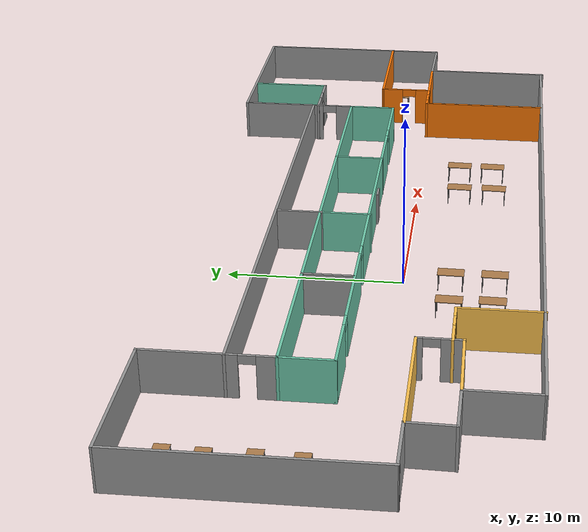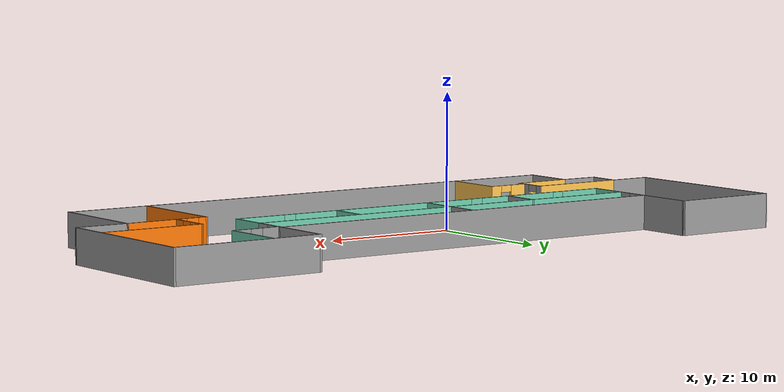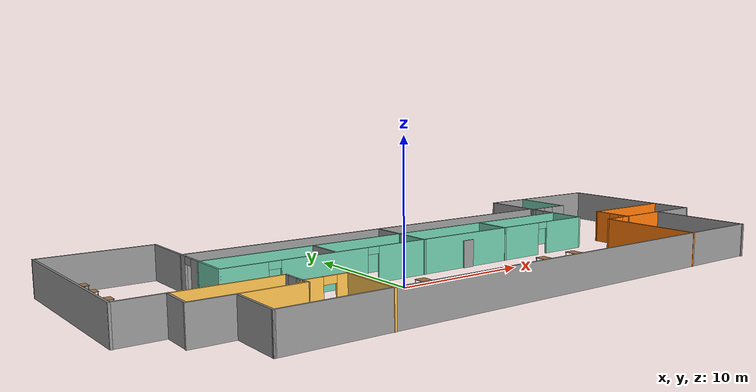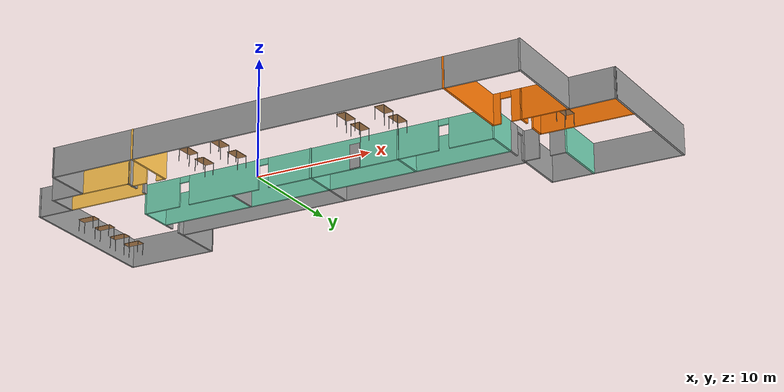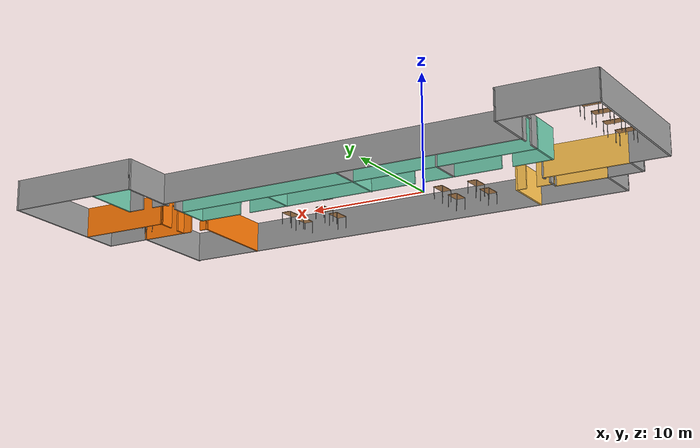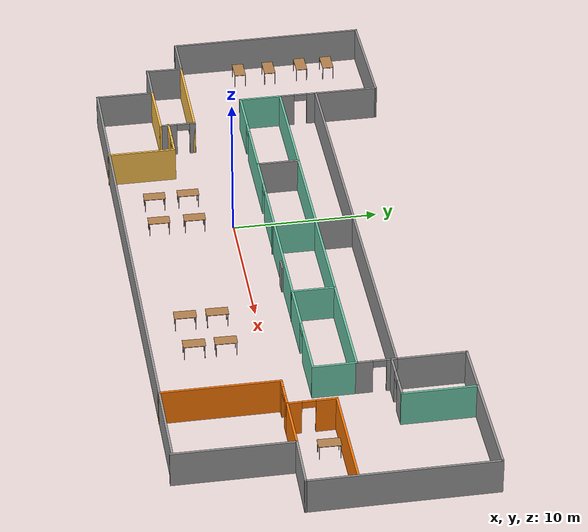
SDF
<?xml version='1.0'?>
<sdf version='1.6'>
  <model name='building'>
    <model name='buildingEditorModel'>
      <pose frame=''>5.31659 2.25421 0 0 -0 0</pose>
      <link name='Door_2'>
        <collision name='Door_2_Collision'>
          <geometry>
            <box>
              <size>0.9 0.17 2</size>
            </box>
          </geometry>
          <pose frame=''>0 0 1 0 -0 0</pose>
        </collision>
        <visual name='Door_2_Visual'>
          <pose frame=''>0 0 1 0 -0 0</pose>
          <geometry>
            <box>
              <size>0.9 0.17 2</size>
            </box>
          </geometry>
          <material>
            <script>
              <uri>file://media/materials/scripts/gazebo.material</uri>
              <name>Gazebo/Grey</name>
            </script>
          </material>
        </visual>
        <pose frame=''>2.1186 -0.056948 0 0 -0 0</pose>
      </link>
      <link name='Wall_12'>
        <collision name='Wall_12_Collision'>
          <geometry>
            <box>
              <size>11.25 0.15 2.5</size>
            </box>
          </geometry>
          <pose frame=''>0 0 1.25 0 -0 0</pose>
        </collision>
        <visual name='Wall_12_Visual'>
          <pose frame=''>0 0 1.25 0 -0 0</pose>
          <geometry>
            <box>
              <size>11.25 0.15 2.5</size>
            </box>
          </geometry>
          <material>
            <script>
              <uri>file://media/materials/scripts/gazebo.material</uri>
              <name>Gazebo/Grey</name>
            </script>
            <ambient>1 1 1 1</ambient>
          </material>
          <meta>
            <layer>0</layer>
          </meta>
        </visual>
        <pose frame=''>19.5996 10.1001 0 0 -0 3.14159</pose>
      </link>
      <link name='Wall_13'>
        <collision name='Wall_13_Collision'>
          <geometry>
            <box>
              <size>4.75 0.15 2.5</size>
            </box>
          </geometry>
          <pose frame=''>0 0 1.25 0 -0 0</pose>
        </collision>
        <visual name='Wall_13_Visual'>
          <pose frame=''>0 0 1.25 0 -0 0</pose>
          <geometry>
            <box>
              <size>4.75 0.15 2.5</size>
            </box>
          </geometry>
          <material>
            <script>
              <uri>file://media/materials/scripts/gazebo.material</uri>
              <name>Gazebo/Grey</name>
            </script>
            <ambient>1 1 1 1</ambient>
          </material>
          <meta>
            <layer>0</layer>
          </meta>
        </visual>
        <pose frame=''>14.0496 7.80012 0 0 -0 -1.5708</pose>
      </link>
      <link name='Wall_14'>
        <collision name='Wall_14_Collision'>
          <geometry>
            <box>
              <size>31.5 0.15 2.5</size>
            </box>
          </geometry>
          <pose frame=''>0 0 1.25 0 -0 0</pose>
        </collision>
        <visual name='Wall_14_Visual'>
          <pose frame=''>0 0 1.25 0 -0 0</pose>
          <geometry>
            <box>
              <size>31.5 0.15 2.5</size>
            </box>
          </geometry>
          <material>
            <script>
              <uri>file://media/materials/scripts/gazebo.material</uri>
              <name>Gazebo/Grey</name>
            </script>
            <ambient>1 1 1 1</ambient>
          </material>
          <meta>
            <layer>0</layer>
          </meta>
        </visual>
        <pose frame=''>-1.62541 5.50012 0 0 -0 3.14159</pose>
      </link>
      <link name='Wall_15'>
        <collision name='Wall_15_Collision'>
          <geometry>
            <box>
              <size>4.5 0.15 2.5</size>
            </box>
          </geometry>
          <pose frame=''>0 0 1.25 0 -0 0</pose>
        </collision>
        <visual name='Wall_15_Visual'>
          <pose frame=''>0 0 1.25 0 -0 0</pose>
          <geometry>
            <box>
              <size>4.5 0.15 2.5</size>
            </box>
          </geometry>
          <material>
            <script>
              <uri>file://media/materials/scripts/gazebo.material</uri>
              <name>Gazebo/Grey</name>
            </script>
            <ambient>1 1 1 1</ambient>
          </material>
          <meta>
            <layer>0</layer>
          </meta>
        </visual>
        <pose frame=''>-17.3004 7.67512 0 0 -0 1.5708</pose>
      </link>
      <link name='Wall_18'>
        <collision name='Wall_18_Collision'>
          <geometry>
            <box>
              <size>8.00016 0.15 2.5</size>
            </box>
          </geometry>
          <pose frame=''>0 0 1.25 0 -0 0</pose>
        </collision>
        <visual name='Wall_18_Visual'>
          <pose frame=''>0 0 1.25 0 -0 0</pose>
          <geometry>
            <box>
              <size>8.00016 0.15 2.5</size>
            </box>
          </geometry>
          <material>
            <script>
              <uri>file://media/materials/scripts/gazebo.material</uri>
              <name>Gazebo/Grey</name>
            </script>
            <ambient>1 1 1 1</ambient>
          </material>
          <meta>
            <layer>0</layer>
          </meta>
        </visual>
        <pose frame=''>-21.2254 9.82512 0 0 -0 0.006369</pose>
      </link>
      <link name='Wall_20'>
        <pose frame=''>-17.3004 4.20012 0 0 -0 -1.5708</pose>
        <visual name='Wall_20_Visual_0'>
          <pose frame=''>-1.00181 0 1.25 0 -0 0</pose>
          <geometry>
            <box>
              <size>0.746388 0.15 2.5</size>
            </box>
          </geometry>
          <material>
            <script>
              <uri>file://media/materials/scripts/gazebo.material</uri>
              <name>Gazebo/Grey</name>
            </script>
            <ambient>1 1 1 1</ambient>
          </material>
          <meta>
            <layer>0</layer>
          </meta>
        </visual>
        <collision name='Wall_20_Collision_0'>
          <geometry>
            <box>
              <size>0.746388 0.15 2.5</size>
            </box>
          </geometry>
          <pose frame=''>-1.00181 0 1.25 0 -0 0</pose>
        </collision>
        <visual name='Wall_20_Visual_1'>
          <pose frame=''>0.823194 0 1.25 0 -0 0</pose>
          <geometry>
            <box>
              <size>1.10361 0.15 2.5</size>
            </box>
          </geometry>
          <material>
            <script>
              <uri>file://media/materials/scripts/gazebo.material</uri>
              <name>Gazebo/Grey</name>
            </script>
            <ambient>1 1 1 1</ambient>
          </material>
          <meta>
            <layer>0</layer>
          </meta>
        </visual>
        <collision name='Wall_20_Collision_1'>
          <geometry>
            <box>
              <size>1.10361 0.15 2.5</size>
            </box>
          </geometry>
          <pose frame=''>0.823194 0 1.25 0 -0 0</pose>
        </collision>
        <visual name='Wall_20_Visual_2'>
          <pose frame=''>-0.178612 0 2.25 0 -0 0</pose>
          <geometry>
            <box>
              <size>0.9 0.15 0.5</size>
            </box>
          </geometry>
          <material>
            <script>
              <uri>file://media/materials/scripts/gazebo.material</uri>
              <name>Gazebo/Grey</name>
            </script>
            <ambient>1 1 1 1</ambient>
          </material>
          <meta>
            <layer>0</layer>
          </meta>
        </visual>
        <collision name='Wall_20_Collision_2'>
          <geometry>
            <box>
              <size>0.9 0.15 0.5</size>
            </box>
          </geometry>
          <pose frame=''>-0.178612 0 2.25 0 -0 0</pose>
        </collision>
      </link>
      <link name='Wall_21'>
        <collision name='Wall_21_Collision'>
          <geometry>
            <box>
              <size>31.5 0.15 2.5</size>
            </box>
          </geometry>
          <pose frame=''>0 0 1.25 0 -0 0</pose>
        </collision>
        <visual name='Wall_21_Visual'>
          <pose frame=''>0 0 1.25 0 -0 0</pose>
          <geometry>
            <box>
              <size>31.5 0.15 2.5</size>
            </box>
          </geometry>
          <material>
            <script>
              <uri>file://media/materials/scripts/gazebo.material</uri>
              <name>Gazebo/Grey</name>
            </script>
            <ambient>0.435294 0.796078 0.67451 1</ambient>
          </material>
          <meta>
            <layer>0</layer>
          </meta>
        </visual>
        <pose frame=''>-1.62541 2.90012 0 0 -0 0</pose>
      </link>
      <link name='Wall_22'>
        <pose frame=''>14.0496 4.20012 0 0 -0 1.5708</pose>
        <visual name='Wall_22_Visual_0'>
          <pose frame=''>-0.810224 0 1.25 0 -0 0</pose>
          <geometry>
            <box>
              <size>1.12955 0.15 2.5</size>
            </box>
          </geometry>
          <material>
            <script>
              <uri>file://media/materials/scripts/gazebo.material</uri>
              <name>Gazebo/Grey</name>
            </script>
            <ambient>1 1 1 1</ambient>
          </material>
          <meta>
            <layer>0</layer>
          </meta>
        </visual>
        <collision name='Wall_22_Collision_0'>
          <geometry>
            <box>
              <size>1.12955 0.15 2.5</size>
            </box>
          </geometry>
          <pose frame=''>-0.810224 0 1.25 0 -0 0</pose>
        </collision>
        <visual name='Wall_22_Visual_1'>
          <pose frame=''>1.01478 0 1.25 0 -0 0</pose>
          <geometry>
            <box>
              <size>0.720448 0.15 2.5</size>
            </box>
          </geometry>
          <material>
            <script>
              <uri>file://media/materials/scripts/gazebo.material</uri>
              <name>Gazebo/Grey</name>
            </script>
            <ambient>1 1 1 1</ambient>
          </material>
          <meta>
            <layer>0</layer>
          </meta>
        </visual>
        <collision name='Wall_22_Collision_1'>
          <geometry>
            <box>
              <size>0.720448 0.15 2.5</size>
            </box>
          </geometry>
          <pose frame=''>1.01478 0 1.25 0 -0 0</pose>
        </collision>
        <visual name='Wall_22_Visual_2'>
          <pose frame=''>0.204552 0 2.25 0 -0 0</pose>
          <geometry>
            <box>
              <size>0.9 0.15 0.5</size>
            </box>
          </geometry>
          <material>
            <script>
              <uri>file://media/materials/scripts/gazebo.material</uri>
              <name>Gazebo/Grey</name>
            </script>
            <ambient>1 1 1 1</ambient>
          </material>
          <meta>
            <layer>0</layer>
          </meta>
        </visual>
        <collision name='Wall_22_Collision_2'>
          <geometry>
            <box>
              <size>0.9 0.15 0.5</size>
            </box>
          </geometry>
          <pose frame=''>0.204552 0 2.25 0 -0 0</pose>
        </collision>
      </link>
      <link name='Wall_24'>
        <collision name='Wall_24_Collision'>
          <geometry>
            <box>
              <size>3 0.15 2.5</size>
            </box>
          </geometry>
          <pose frame=''>0 0 1.25 0 -0 0</pose>
        </collision>
        <visual name='Wall_24_Visual'>
          <pose frame=''>0 0 1.25 0 -0 0</pose>
          <geometry>
            <box>
              <size>3 0.15 2.5</size>
            </box>
          </geometry>
          <material>
            <script>
              <uri>file://media/materials/scripts/gazebo.material</uri>
              <name>Gazebo/Grey</name>
            </script>
            <ambient>0.435294 0.796078 0.67451 1</ambient>
          </material>
          <meta>
            <layer>0</layer>
          </meta>
        </visual>
        <pose frame=''>-17.3004 1.47512 0 0 -0 -1.5708</pose>
      </link>
      <link name='Wall_25'>
        <pose frame=''>-1.62541 0.050122 0 0 -0 0</pose>
        <visual name='Wall_25_Visual_0'>
          <pose frame=''>-14.0877 0 1.25 0 -0 0</pose>
          <geometry>
            <box>
              <size>3.32458 0.15 2.5</size>
            </box>
          </geometry>
          <material>
            <script>
              <uri>file://media/materials/scripts/gazebo.material</uri>
              <name>Gazebo/Grey</name>
            </script>
            <ambient>0.435294 0.796078 0.67451 1</ambient>
          </material>
          <meta>
            <layer>0</layer>
          </meta>
        </visual>
        <collision name='Wall_25_Collision_0'>
          <geometry>
            <box>
              <size>3.32458 0.15 2.5</size>
            </box>
          </geometry>
          <pose frame=''>-14.0877 0 1.25 0 -0 0</pose>
        </collision>
        <visual name='Wall_25_Visual_1'>
          <pose frame=''>-8.27902 0 1.25 0 -0 0</pose>
          <geometry>
            <box>
              <size>6.4928 0.15 2.5</size>
            </box>
          </geometry>
          <material>
            <script>
              <uri>file://media/materials/scripts/gazebo.material</uri>
              <name>Gazebo/Grey</name>
            </script>
            <ambient>0.435294 0.796078 0.67451 1</ambient>
          </material>
          <meta>
            <layer>0</layer>
          </meta>
        </visual>
        <collision name='Wall_25_Collision_1'>
          <geometry>
            <box>
              <size>6.4928 0.15 2.5</size>
            </box>
          </geometry>
          <pose frame=''>-8.27902 0 1.25 0 -0 0</pose>
        </collision>
        <visual name='Wall_25_Visual_2'>
          <pose frame=''>3.43273 0 1.25 0 -0 0</pose>
          <geometry>
            <box>
              <size>15.1307 0.15 2.5</size>
            </box>
          </geometry>
          <material>
            <script>
              <uri>file://media/materials/scripts/gazebo.material</uri>
              <name>Gazebo/Grey</name>
            </script>
            <ambient>0.435294 0.796078 0.67451 1</ambient>
          </material>
          <meta>
            <layer>0</layer>
          </meta>
        </visual>
        <collision name='Wall_25_Collision_2'>
          <geometry>
            <box>
              <size>15.1307 0.15 2.5</size>
            </box>
          </geometry>
          <pose frame=''>3.43273 0 1.25 0 -0 0</pose>
        </collision>
        <visual name='Wall_25_Visual_3'>
          <pose frame=''>13.824 0 1.25 0 -0 0</pose>
          <geometry>
            <box>
              <size>3.85191 0.15 2.5</size>
            </box>
          </geometry>
          <material>
            <script>
              <uri>file://media/materials/scripts/gazebo.material</uri>
              <name>Gazebo/Grey</name>
            </script>
            <ambient>0.435294 0.796078 0.67451 1</ambient>
          </material>
          <meta>
            <layer>0</layer>
          </meta>
        </visual>
        <collision name='Wall_25_Collision_3'>
          <geometry>
            <box>
              <size>3.85191 0.15 2.5</size>
            </box>
          </geometry>
          <pose frame=''>13.824 0 1.25 0 -0 0</pose>
        </collision>
        <visual name='Wall_25_Visual_4'>
          <pose frame=''>-11.9754 0 2.25 0 -0 0</pose>
          <geometry>
            <box>
              <size>0.9 0.15 0.5</size>
            </box>
          </geometry>
          <material>
            <script>
              <uri>file://media/materials/scripts/gazebo.material</uri>
              <name>Gazebo/Grey</name>
            </script>
            <ambient>0.435294 0.796078 0.67451 1</ambient>
          </material>
          <meta>
            <layer>0</layer>
          </meta>
        </visual>
        <collision name='Wall_25_Collision_4'>
          <geometry>
            <box>
              <size>0.9 0.15 0.5</size>
            </box>
          </geometry>
          <pose frame=''>-11.9754 0 2.25 0 -0 0</pose>
        </collision>
        <visual name='Wall_25_Visual_5'>
          <pose frame=''>-4.58262 0 2.25 0 -0 0</pose>
          <geometry>
            <box>
              <size>0.9 0.15 0.5</size>
            </box>
          </geometry>
          <material>
            <script>
              <uri>file://media/materials/scripts/gazebo.material</uri>
              <name>Gazebo/Grey</name>
            </script>
            <ambient>0.435294 0.796078 0.67451 1</ambient>
          </material>
          <meta>
            <layer>0</layer>
          </meta>
        </visual>
        <collision name='Wall_25_Collision_5'>
          <geometry>
            <box>
              <size>0.9 0.15 0.5</size>
            </box>
          </geometry>
          <pose frame=''>-4.58262 0 2.25 0 -0 0</pose>
        </collision>
        <visual name='Wall_25_Visual_6'>
          <pose frame=''>11.4481 0 2.25 0 -0 0</pose>
          <geometry>
            <box>
              <size>0.9 0.15 0.5</size>
            </box>
          </geometry>
          <material>
            <script>
              <uri>file://media/materials/scripts/gazebo.material</uri>
              <name>Gazebo/Grey</name>
            </script>
            <ambient>0.435294 0.796078 0.67451 1</ambient>
          </material>
          <meta>
            <layer>0</layer>
          </meta>
        </visual>
        <collision name='Wall_25_Collision_6'>
          <geometry>
            <box>
              <size>0.9 0.15 0.5</size>
            </box>
          </geometry>
          <pose frame=''>11.4481 0 2.25 0 -0 0</pose>
        </collision>
      </link>
      <link name='Wall_26'>
        <collision name='Wall_26_Collision'>
          <geometry>
            <box>
              <size>3 0.15 2.5</size>
            </box>
          </geometry>
          <pose frame=''>0 0 1.25 0 -0 0</pose>
        </collision>
        <visual name='Wall_26_Visual'>
          <pose frame=''>0 0 1.25 0 -0 0</pose>
          <geometry>
            <box>
              <size>3 0.15 2.5</size>
            </box>
          </geometry>
          <material>
            <script>
              <uri>file://media/materials/scripts/gazebo.material</uri>
              <name>Gazebo/Grey</name>
            </script>
            <ambient>0.435294 0.796078 0.67451 1</ambient>
          </material>
          <meta>
            <layer>0</layer>
          </meta>
        </visual>
        <pose frame=''>14.0496 1.47512 0 0 -0 1.5708</pose>
      </link>
      <link name='Wall_28'>
        <collision name='Wall_28_Collision'>
          <geometry>
            <box>
              <size>2.75 0.15 2.5</size>
            </box>
          </geometry>
          <pose frame=''>0 0 1.25 0 -0 0</pose>
        </collision>
        <visual name='Wall_28_Visual'>
          <pose frame=''>0 0 1.25 0 -0 0</pose>
          <geometry>
            <box>
              <size>2.75 0.15 2.5</size>
            </box>
          </geometry>
          <material>
            <script>
              <uri>file://media/materials/scripts/gazebo.material</uri>
              <name>Gazebo/Grey</name>
            </script>
            <ambient>1 1 1 1</ambient>
          </material>
          <meta>
            <layer>0</layer>
          </meta>
        </visual>
        <pose frame=''>-1.8761 4.11632 0 0 -0 -1.5708</pose>
      </link>
      <link name='Wall_30'>
        <collision name='Wall_30_Collision'>
          <geometry>
            <box>
              <size>3 0.15 2.5</size>
            </box>
          </geometry>
          <pose frame=''>0 0 1.25 0 -0 0</pose>
        </collision>
        <visual name='Wall_30_Visual'>
          <pose frame=''>0 0 1.25 0 -0 0</pose>
          <geometry>
            <box>
              <size>3 0.15 2.5</size>
            </box>
          </geometry>
          <material>
            <script>
              <uri>file://media/materials/scripts/gazebo.material</uri>
              <name>Gazebo/Grey</name>
            </script>
            <ambient>1 1 1 1</ambient>
          </material>
          <meta>
            <layer>0</layer>
          </meta>
        </visual>
        <pose frame=''>-9.11327 1.47517 0 0 -0 -1.5708</pose>
      </link>
      <link name='Wall_34'>
        <collision name='Wall_34_Collision'>
          <geometry>
            <box>
              <size>3 0.15 2.5</size>
            </box>
          </geometry>
          <pose frame=''>0 0 1.25 0 -0 0</pose>
        </collision>
        <visual name='Wall_34_Visual'>
          <pose frame=''>0 0 1.25 0 -0 0</pose>
          <geometry>
            <box>
              <size>3 0.15 2.5</size>
            </box>
          </geometry>
          <material>
            <script>
              <uri>file://media/materials/scripts/gazebo.material</uri>
              <name>Gazebo/Grey</name>
            </script>
            <ambient>0.435294 0.796078 0.67451 1</ambient>
          </material>
          <meta>
            <layer>0</layer>
          </meta>
        </visual>
        <pose frame=''>-1.8761 1.39132 0 0 -0 -1.5708</pose>
      </link>
      <link name='Wall_36'>
        <collision name='Wall_36_Collision'>
          <geometry>
            <box>
              <size>3 0.15 2.5</size>
            </box>
          </geometry>
          <pose frame=''>0 0 1.25 0 -0 0</pose>
        </collision>
        <visual name='Wall_36_Visual'>
          <pose frame=''>0 0 1.25 0 -0 0</pose>
          <geometry>
            <box>
              <size>3 0.15 2.5</size>
            </box>
          </geometry>
          <material>
            <script>
              <uri>file://media/materials/scripts/gazebo.material</uri>
              <name>Gazebo/Grey</name>
            </script>
            <ambient>0.435294 0.796078 0.67451 1</ambient>
          </material>
          <meta>
            <layer>0</layer>
          </meta>
        </visual>
        <pose frame=''>5.85391 1.44923 0 0 -0 -1.5708</pose>
      </link>
      <link name='Wall_38'>
        <collision name='Wall_38_Collision'>
          <geometry>
            <box>
              <size>12.5 0.15 2.5</size>
            </box>
          </geometry>
          <pose frame=''>0 0 1.25 0 -0 0</pose>
        </collision>
        <visual name='Wall_38_Visual'>
          <pose frame=''>0 0 1.25 0 -0 0</pose>
          <geometry>
            <box>
              <size>12.5 0.15 2.5</size>
            </box>
          </geometry>
          <material>
            <script>
              <uri>file://media/materials/scripts/gazebo.material</uri>
              <name>Gazebo/Grey</name>
            </script>
            <ambient>1 1 1 1</ambient>
          </material>
          <meta>
            <layer>0</layer>
          </meta>
        </visual>
        <pose frame=''>25.1496 3.92512 0 0 -0 -1.5708</pose>
      </link>
      <link name='Wall_39'>
        <collision name='Wall_39_Collision'>
          <geometry>
            <box>
              <size>3.97441 0.15 2.5</size>
            </box>
          </geometry>
          <pose frame=''>0 0 1.25 0 -0 0</pose>
        </collision>
        <visual name='Wall_39_Visual'>
          <pose frame=''>0 0 1.25 0 -0 0</pose>
          <geometry>
            <box>
              <size>3.97441 0.15 2.5</size>
            </box>
          </geometry>
          <material>
            <script>
              <uri>file://media/materials/scripts/gazebo.material</uri>
              <name>Gazebo/Grey</name>
            </script>
            <ambient>1 1 1 1</ambient>
          </material>
          <meta>
            <layer>0</layer>
          </meta>
        </visual>
        <pose frame=''>23.2376 -2.21097 0 0 -0 3.12125</pose>
      </link>
      <link name='Wall_40'>
        <collision name='Wall_40_Collision'>
          <geometry>
            <box>
              <size>8.07786 0.15 2.5</size>
            </box>
          </geometry>
          <pose frame=''>0 0 1.25 0 -0 0</pose>
        </collision>
        <visual name='Wall_40_Visual'>
          <pose frame=''>0 0 1.25 0 -0 0</pose>
          <geometry>
            <box>
              <size>8.07786 0.15 2.5</size>
            </box>
          </geometry>
          <material>
            <script>
              <uri>file://media/materials/scripts/gazebo.material</uri>
              <name>Gazebo/Grey</name>
            </script>
            <ambient>1 1 1 1</ambient>
          </material>
          <meta>
            <layer>0</layer>
          </meta>
        </visual>
        <pose frame=''>21.3126 -6.13597 0 0 -0 -1.57407</pose>
      </link>
      <link name='Wall_42'>
        <collision name='Wall_42_Collision'>
          <geometry>
            <box>
              <size>40.5 0.15 2.5</size>
            </box>
          </geometry>
          <pose frame=''>0 0 1.25 0 -0 0</pose>
        </collision>
        <visual name='Wall_42_Visual'>
          <pose frame=''>0 0 1.25 0 -0 0</pose>
          <geometry>
            <box>
              <size>40.5 0.15 2.5</size>
            </box>
          </geometry>
          <material>
            <script>
              <uri>file://media/materials/scripts/gazebo.material</uri>
              <name>Gazebo/Grey</name>
            </script>
            <ambient>1 1 1 1</ambient>
          </material>
          <meta>
            <layer>0</layer>
          </meta>
        </visual>
        <pose frame=''>0.974593 -9.99988 0 0 -0 0</pose>
      </link>
      <link name='Wall_45'>
        <collision name='Wall_45_Collision'>
          <geometry>
            <box>
              <size>7.25 0.15 2.5</size>
            </box>
          </geometry>
          <pose frame=''>0 0 1.25 0 -0 0</pose>
        </collision>
        <visual name='Wall_45_Visual'>
          <pose frame=''>0 0 1.25 0 -0 0</pose>
          <geometry>
            <box>
              <size>7.25 0.15 2.5</size>
            </box>
          </geometry>
          <material>
            <script>
              <uri>file://media/materials/scripts/gazebo.material</uri>
              <name>Gazebo/Grey</name>
            </script>
            <ambient>1 0.764706 0.305882 1</ambient>
          </material>
          <meta>
            <layer>0</layer>
          </meta>
        </visual>
        <pose frame=''>-18.4226 -3.61565 0 0 -0 0</pose>
      </link>
      <link name='Wall_46'>
        <pose frame=''>-14.8726 -4.81659 0 0 -0 -1.5708</pose>
        <visual name='Wall_46_Visual_0'>
          <pose frame=''>-1.06386 0 1.25 0 -0 0</pose>
          <geometry>
            <box>
              <size>0.424155 0.15 2.5</size>
            </box>
          </geometry>
          <material>
            <script>
              <uri>file://media/materials/scripts/gazebo.material</uri>
              <name>Gazebo/Grey</name>
            </script>
            <ambient>1 1 1 1</ambient>
          </material>
          <meta>
            <layer>0</layer>
          </meta>
        </visual>
        <collision name='Wall_46_Collision_0'>
          <geometry>
            <box>
              <size>0.424155 0.15 2.5</size>
            </box>
          </geometry>
          <pose frame=''>-1.06386 0 1.25 0 -0 0</pose>
        </collision>
        <visual name='Wall_46_Visual_1'>
          <pose frame=''>0.662078 0 1.25 0 -0 0</pose>
          <geometry>
            <box>
              <size>1.22772 0.15 2.5</size>
            </box>
          </geometry>
          <material>
            <script>
              <uri>file://media/materials/scripts/gazebo.material</uri>
              <name>Gazebo/Grey</name>
            </script>
            <ambient>1 1 1 1</ambient>
          </material>
          <meta>
            <layer>0</layer>
          </meta>
        </visual>
        <collision name='Wall_46_Collision_1'>
          <geometry>
            <box>
              <size>1.22772 0.15 2.5</size>
            </box>
          </geometry>
          <pose frame=''>0.662078 0 1.25 0 -0 0</pose>
        </collision>
        <visual name='Wall_46_Visual_2'>
          <pose frame=''>-0.401784 0 2.25 0 -0 0</pose>
          <geometry>
            <box>
              <size>0.9 0.15 0.5</size>
            </box>
          </geometry>
          <material>
            <script>
              <uri>file://media/materials/scripts/gazebo.material</uri>
              <name>Gazebo/Grey</name>
            </script>
            <ambient>1 1 1 1</ambient>
          </material>
          <meta>
            <layer>0</layer>
          </meta>
        </visual>
        <collision name='Wall_46_Collision_2'>
          <geometry>
            <box>
              <size>0.9 0.15 0.5</size>
            </box>
          </geometry>
          <pose frame=''>-0.401784 0 2.25 0 -0 0</pose>
        </collision>
      </link>
      <link name='Wall_47'>
        <collision name='Wall_47_Collision'>
          <geometry>
            <box>
              <size>4.45217 0.15 2.5</size>
            </box>
          </geometry>
          <pose frame=''>0 0 1.25 0 -0 0</pose>
        </collision>
        <visual name='Wall_47_Visual'>
          <pose frame=''>0 0 1.25 0 -0 0</pose>
          <geometry>
            <box>
              <size>4.45217 0.15 2.5</size>
            </box>
          </geometry>
          <material>
            <script>
              <uri>file://media/materials/scripts/gazebo.material</uri>
              <name>Gazebo/Grey</name>
            </script>
            <ambient>1 0.764706 0.305882 1</ambient>
          </material>
          <meta>
            <layer>0</layer>
          </meta>
        </visual>
        <pose frame=''>-16.9976 -6.04235 0 0 -0 -3.13006</pose>
      </link>
      <link name='Wall_5'>
        <collision name='Wall_5_Collision'>
          <geometry>
            <box>
              <size>13.566 0.15 2.5</size>
            </box>
          </geometry>
          <pose frame=''>0 0 1.25 0 -0 0</pose>
        </collision>
        <visual name='Wall_5_Visual'>
          <pose frame=''>0 0 1.25 0 -0 0</pose>
          <geometry>
            <box>
              <size>13.566 0.15 2.5</size>
            </box>
          </geometry>
          <material>
            <script>
              <uri>file://media/materials/scripts/gazebo.material</uri>
              <name>Gazebo/Grey</name>
            </script>
            <ambient>1 1 1 1</ambient>
          </material>
          <meta>
            <layer>0</layer>
          </meta>
        </visual>
        <pose frame=''>-25.1115 3.09223 0 0 -0 -1.565</pose>
      </link>
      <link name='Wall_51'>
        <pose frame=''>-13.3738 -5.4524 0 0 -0 0</pose>
        <visual name='Wall_51_Visual_0'>
          <pose frame=''>-0.891642 0 1.25 0 -0 0</pose>
          <geometry>
            <box>
              <size>1.46672 0.15 2.5</size>
            </box>
          </geometry>
          <material>
            <script>
              <uri>file://media/materials/scripts/gazebo.material</uri>
              <name>Gazebo/Grey</name>
            </script>
            <ambient>1 0.764706 0.305882 1</ambient>
          </material>
          <meta>
            <layer>0</layer>
          </meta>
        </visual>
        <collision name='Wall_51_Collision_0'>
          <geometry>
            <box>
              <size>1.46672 0.15 2.5</size>
            </box>
          </geometry>
          <pose frame=''>-0.891642 0 1.25 0 -0 0</pose>
        </collision>
        <visual name='Wall_51_Visual_1'>
          <pose frame=''>1.18336 0 1.25 0 -0 0</pose>
          <geometry>
            <box>
              <size>0.883284 0.15 2.5</size>
            </box>
          </geometry>
          <material>
            <script>
              <uri>file://media/materials/scripts/gazebo.material</uri>
              <name>Gazebo/Grey</name>
            </script>
            <ambient>1 0.764706 0.305882 1</ambient>
          </material>
          <meta>
            <layer>0</layer>
          </meta>
        </visual>
        <collision name='Wall_51_Collision_1'>
          <geometry>
            <box>
              <size>0.883284 0.15 2.5</size>
            </box>
          </geometry>
          <pose frame=''>1.18336 0 1.25 0 -0 0</pose>
        </collision>
        <visual name='Wall_51_Visual_2'>
          <pose frame=''>0.291716 0 2.25 0 -0 0</pose>
          <geometry>
            <box>
              <size>0.9 0.15 0.5</size>
            </box>
          </geometry>
          <material>
            <script>
              <uri>file://media/materials/scripts/gazebo.material</uri>
              <name>Gazebo/Grey</name>
            </script>
            <ambient>1 0.764706 0.305882 1</ambient>
          </material>
          <meta>
            <layer>0</layer>
          </meta>
        </visual>
        <collision name='Wall_51_Collision_2'>
          <geometry>
            <box>
              <size>0.9 0.15 0.5</size>
            </box>
          </geometry>
          <pose frame=''>0.291716 0 2.25 0 -0 0</pose>
        </collision>
      </link>
      <link name='Wall_52'>
        <collision name='Wall_52_Collision'>
          <geometry>
            <box>
              <size>4.75 0.15 2.5</size>
            </box>
          </geometry>
          <pose frame=''>0 0 1.25 0 -0 0</pose>
        </collision>
        <visual name='Wall_52_Visual'>
          <pose frame=''>0 0 1.25 0 -0 0</pose>
          <geometry>
            <box>
              <size>4.75 0.15 2.5</size>
            </box>
          </geometry>
          <material>
            <script>
              <uri>file://media/materials/scripts/gazebo.material</uri>
              <name>Gazebo/Grey</name>
            </script>
            <ambient>1 0.764706 0.305882 1</ambient>
          </material>
          <meta>
            <layer>0</layer>
          </meta>
        </visual>
        <pose frame=''>-11.8238 -7.7524 0 0 -0 -1.5708</pose>
      </link>
      <link name='Wall_54'>
        <collision name='Wall_54_Collision'>
          <geometry>
            <box>
              <size>7.75 0.15 2.5</size>
            </box>
          </geometry>
          <pose frame=''>0 0 1.25 0 -0 0</pose>
        </collision>
        <visual name='Wall_54_Visual'>
          <pose frame=''>0 0 1.25 0 -0 0</pose>
          <geometry>
            <box>
              <size>7.75 0.15 2.5</size>
            </box>
          </geometry>
          <material>
            <script>
              <uri>file://media/materials/scripts/gazebo.material</uri>
              <name>Gazebo/Grey</name>
            </script>
            <ambient>0.996078 0.47451 0.0196078 1</ambient>
          </material>
          <meta>
            <layer>0</layer>
          </meta>
        </visual>
        <pose frame=''>21.2493 1.03252 0 0 -0 3.14159</pose>
      </link>
      <link name='Wall_58'>
        <collision name='Wall_58_Collision'>
          <geometry>
            <box>
              <size>4 0.15 2.5</size>
            </box>
          </geometry>
          <pose frame=''>0 0 1.25 0 -0 0</pose>
        </collision>
        <visual name='Wall_58_Visual'>
          <pose frame=''>0 0 1.25 0 -0 0</pose>
          <geometry>
            <box>
              <size>4 0.15 2.5</size>
            </box>
          </geometry>
          <material>
            <script>
              <uri>file://media/materials/scripts/gazebo.material</uri>
              <name>Gazebo/Grey</name>
            </script>
            <ambient>0.996078 0.47451 0.0196078 1</ambient>
          </material>
          <meta>
            <layer>0</layer>
          </meta>
        </visual>
        <pose frame=''>19.4005 -2.17206 0 0 -0 3.14159</pose>
      </link>
      <link name='Wall_59'>
        <pose frame=''>17.4624 -0.569771 0 0 -0 1.57899</pose>
        <visual name='Wall_59_Visual_0'>
          <pose frame=''>-1.17025 0 1.25 0 -0 0</pose>
          <geometry>
            <box>
              <size>1.01419 0.15 2.5</size>
            </box>
          </geometry>
          <material>
            <script>
              <uri>file://media/materials/scripts/gazebo.material</uri>
              <name>Gazebo/Grey</name>
            </script>
            <ambient>0.996078 0.47451 0.0196078 1</ambient>
          </material>
          <meta>
            <layer>0</layer>
          </meta>
        </visual>
        <collision name='Wall_59_Collision_0'>
          <geometry>
            <box>
              <size>1.01419 0.15 2.5</size>
            </box>
          </geometry>
          <pose frame=''>-1.17025 0 1.25 0 -0 0</pose>
        </collision>
        <visual name='Wall_59_Visual_1'>
          <pose frame=''>0.957093 0 1.25 0 -0 0</pose>
          <geometry>
            <box>
              <size>1.4405 0.15 2.5</size>
            </box>
          </geometry>
          <material>
            <script>
              <uri>file://media/materials/scripts/gazebo.material</uri>
              <name>Gazebo/Grey</name>
            </script>
            <ambient>0.996078 0.47451 0.0196078 1</ambient>
          </material>
          <meta>
            <layer>0</layer>
          </meta>
        </visual>
        <collision name='Wall_59_Collision_1'>
          <geometry>
            <box>
              <size>1.4405 0.15 2.5</size>
            </box>
          </geometry>
          <pose frame=''>0.957093 0 1.25 0 -0 0</pose>
        </collision>
        <visual name='Wall_59_Visual_2'>
          <pose frame=''>-0.213157 0 2.25 0 -0 0</pose>
          <geometry>
            <box>
              <size>0.9 0.15 0.5</size>
            </box>
          </geometry>
          <material>
            <script>
              <uri>file://media/materials/scripts/gazebo.material</uri>
              <name>Gazebo/Grey</name>
            </script>
            <ambient>0.996078 0.47451 0.0196078 1</ambient>
          </material>
          <meta>
            <layer>0</layer>
          </meta>
        </visual>
        <collision name='Wall_59_Collision_2'>
          <geometry>
            <box>
              <size>0.9 0.15 0.5</size>
            </box>
          </geometry>
          <pose frame=''>-0.213157 0 2.25 0 -0 0</pose>
        </collision>
      </link>
      <link name='Wall_6'>
        <collision name='Wall_6_Collision'>
          <geometry>
            <box>
              <size>3.25 0.15 2.5</size>
            </box>
          </geometry>
          <pose frame=''>0 0 1.25 0 -0 0</pose>
        </collision>
        <visual name='Wall_6_Visual'>
          <pose frame=''>0 0 1.25 0 -0 0</pose>
          <geometry>
            <box>
              <size>3.25 0.15 2.5</size>
            </box>
          </geometry>
          <material>
            <script>
              <uri>file://media/materials/scripts/gazebo.material</uri>
              <name>Gazebo/Grey</name>
            </script>
            <ambient>1 1 1 1</ambient>
          </material>
          <meta>
            <layer>0</layer>
          </meta>
        </visual>
        <pose frame=''>-23.5226 -3.58971 0 0 -0 0</pose>
      </link>
      <link name='Wall_62'>
        <pose frame=''>16.3005 -2.17206 0 0 -0 3.14159</pose>
        <visual name='Wall_62_Visual_0'>
          <pose frame=''>-0.814621 0 1.25 0 -0 0</pose>
          <geometry>
            <box>
              <size>0.870759 0.15 2.5</size>
            </box>
          </geometry>
          <material>
            <script>
              <uri>file://media/materials/scripts/gazebo.material</uri>
              <name>Gazebo/Grey</name>
            </script>
            <ambient>0.996078 0.47451 0.0196078 1</ambient>
          </material>
          <meta>
            <layer>0</layer>
          </meta>
        </visual>
        <collision name='Wall_62_Collision_0'>
          <geometry>
            <box>
              <size>0.870759 0.15 2.5</size>
            </box>
          </geometry>
          <pose frame=''>-0.814621 0 1.25 0 -0 0</pose>
        </collision>
        <visual name='Wall_62_Visual_1'>
          <pose frame=''>0.885379 0 1.25 0 -0 0</pose>
          <geometry>
            <box>
              <size>0.729241 0.15 2.5</size>
            </box>
          </geometry>
          <material>
            <script>
              <uri>file://media/materials/scripts/gazebo.material</uri>
              <name>Gazebo/Grey</name>
            </script>
            <ambient>0.996078 0.47451 0.0196078 1</ambient>
          </material>
          <meta>
            <layer>0</layer>
          </meta>
        </visual>
        <collision name='Wall_62_Collision_1'>
          <geometry>
            <box>
              <size>0.729241 0.15 2.5</size>
            </box>
          </geometry>
          <pose frame=''>0.885379 0 1.25 0 -0 0</pose>
        </collision>
        <visual name='Wall_62_Visual_2'>
          <pose frame=''>0.070759 0 2.25 0 -0 0</pose>
          <geometry>
            <box>
              <size>0.9 0.15 0.5</size>
            </box>
          </geometry>
          <material>
            <script>
              <uri>file://media/materials/scripts/gazebo.material</uri>
              <name>Gazebo/Grey</name>
            </script>
            <ambient>0.996078 0.47451 0.0196078 1</ambient>
          </material>
          <meta>
            <layer>0</layer>
          </meta>
        </visual>
        <collision name='Wall_62_Collision_2'>
          <geometry>
            <box>
              <size>0.9 0.15 0.5</size>
            </box>
          </geometry>
          <pose frame=''>0.070759 0 2.25 0 -0 0</pose>
        </collision>
      </link>
      <link name='Wall_63'>
        <collision name='Wall_63_Collision'>
          <geometry>
            <box>
              <size>8 0.15 2.5</size>
            </box>
          </geometry>
          <pose frame=''>0 0 1.25 0 -0 0</pose>
        </collision>
        <visual name='Wall_63_Visual'>
          <pose frame=''>0 0 1.25 0 -0 0</pose>
          <geometry>
            <box>
              <size>8 0.15 2.5</size>
            </box>
          </geometry>
          <material>
            <script>
              <uri>file://media/materials/scripts/gazebo.material</uri>
              <name>Gazebo/Grey</name>
            </script>
            <ambient>0.996078 0.47451 0.0196078 1</ambient>
          </material>
          <meta>
            <layer>0</layer>
          </meta>
        </visual>
        <pose frame=''>15.1255 -6.09706 0 0 -0 -1.5708</pose>
      </link>
      <link name='Wall_65'>
        <pose frame=''>15.8249 5.18286 0 0 -0 0</pose>
        <visual name='Wall_65_Visual_0'>
          <pose frame=''>-1.16758 0 1.25 0 -0 0</pose>
          <geometry>
            <box>
              <size>1.41484 0.15 2.5</size>
            </box>
          </geometry>
          <material>
            <script>
              <uri>file://media/materials/scripts/gazebo.material</uri>
              <name>Gazebo/Grey</name>
            </script>
            <ambient>1 1 1 1</ambient>
          </material>
          <meta>
            <layer>0</layer>
          </meta>
        </visual>
        <collision name='Wall_65_Collision_0'>
          <geometry>
            <box>
              <size>1.41484 0.15 2.5</size>
            </box>
          </geometry>
          <pose frame=''>-1.16758 0 1.25 0 -0 0</pose>
        </collision>
        <visual name='Wall_65_Visual_1'>
          <pose frame=''>1.15742 0 1.25 0 -0 0</pose>
          <geometry>
            <box>
              <size>1.43516 0.15 2.5</size>
            </box>
          </geometry>
          <material>
            <script>
              <uri>file://media/materials/scripts/gazebo.material</uri>
              <name>Gazebo/Grey</name>
            </script>
            <ambient>1 1 1 1</ambient>
          </material>
          <meta>
            <layer>0</layer>
          </meta>
        </visual>
        <collision name='Wall_65_Collision_1'>
          <geometry>
            <box>
              <size>1.43516 0.15 2.5</size>
            </box>
          </geometry>
          <pose frame=''>1.15742 0 1.25 0 -0 0</pose>
        </collision>
        <visual name='Wall_65_Visual_2'>
          <pose frame=''>-0.010162 0 2.25 0 -0 0</pose>
          <geometry>
            <box>
              <size>0.9 0.15 0.5</size>
            </box>
          </geometry>
          <material>
            <script>
              <uri>file://media/materials/scripts/gazebo.material</uri>
              <name>Gazebo/Grey</name>
            </script>
            <ambient>1 1 1 1</ambient>
          </material>
          <meta>
            <layer>0</layer>
          </meta>
        </visual>
        <collision name='Wall_65_Collision_2'>
          <geometry>
            <box>
              <size>0.9 0.15 0.5</size>
            </box>
          </geometry>
          <pose frame=''>-0.010162 0 2.25 0 -0 0</pose>
        </collision>
      </link>
      <link name='Wall_66'>
        <collision name='Wall_66_Collision'>
          <geometry>
            <box>
              <size>5 0.15 2.5</size>
            </box>
          </geometry>
          <pose frame=''>0 0 1.25 0 -0 0</pose>
        </collision>
        <visual name='Wall_66_Visual'>
          <pose frame=''>0 0 1.25 0 -0 0</pose>
          <geometry>
            <box>
              <size>5 0.15 2.5</size>
            </box>
          </geometry>
          <material>
            <script>
              <uri>file://media/materials/scripts/gazebo.material</uri>
              <name>Gazebo/Grey</name>
            </script>
            <ambient>0.435294 0.796078 0.67451 1</ambient>
          </material>
          <meta>
            <layer>0</layer>
          </meta>
        </visual>
        <pose frame=''>17.6249 7.60786 0 0 -0 1.5708</pose>
      </link>
      <link name='Wall_7'>
        <collision name='Wall_7_Collision'>
          <geometry>
            <box>
              <size>2.55019 0.15 2.5</size>
            </box>
          </geometry>
          <pose frame=''>0 0 1.25 0 -0 0</pose>
        </collision>
        <visual name='Wall_7_Visual'>
          <pose frame=''>0 0 1.25 0 -0 0</pose>
          <geometry>
            <box>
              <size>2.55019 0.15 2.5</size>
            </box>
          </geometry>
          <material>
            <script>
              <uri>file://media/materials/scripts/gazebo.material</uri>
              <name>Gazebo/Grey</name>
            </script>
            <ambient>1 1 1 1</ambient>
          </material>
          <meta>
            <layer>0</layer>
          </meta>
        </visual>
        <pose frame=''>-21.9985 -4.81547 0 0 -0 -1.59241</pose>
      </link>
      <link name='Wall_8'>
        <collision name='Wall_8_Collision'>
          <geometry>
            <box>
              <size>3.02606 0.15 2.5</size>
            </box>
          </geometry>
          <pose frame=''>0 0 1.25 0 -0 0</pose>
        </collision>
        <visual name='Wall_8_Visual'>
          <pose frame=''>0 0 1.25 0 -0 0</pose>
          <geometry>
            <box>
              <size>3.02606 0.15 2.5</size>
            </box>
          </geometry>
          <material>
            <script>
              <uri>file://media/materials/scripts/gazebo.material</uri>
              <name>Gazebo/Grey</name>
            </script>
            <ambient>1 1 1 1</ambient>
          </material>
          <meta>
            <layer>0</layer>
          </meta>
        </visual>
        <pose frame=''>-20.6124 -6.05419 0 0 -0 -0.009019</pose>
      </link>
      <link name='Wall_9'>
        <collision name='Wall_9_Collision'>
          <geometry>
            <box>
              <size>4.0828 0.15 2.5</size>
            </box>
          </geometry>
          <pose frame=''>0 0 1.25 0 -0 0</pose>
        </collision>
        <visual name='Wall_9_Visual'>
          <pose frame=''>0 0 1.25 0 -0 0</pose>
          <geometry>
            <box>
              <size>4.0828 0.15 2.5</size>
            </box>
          </geometry>
          <material>
            <script>
              <uri>file://media/materials/scripts/gazebo.material</uri>
              <name>Gazebo/Grey</name>
            </script>
            <ambient>1 1 1 1</ambient>
          </material>
          <meta>
            <layer>0</layer>
          </meta>
        </visual>
        <pose frame=''>-19.1874 -8.03352 0 0 -0 -1.57739</pose>
      </link>
      <static>1</static>
    </model>
    <model name='table'>
      <static>1</static>
      <link name='link'>
        <collision name='surface'>
          <pose frame=''>0 0 1 0 -0 0</pose>
          <geometry>
            <box>
              <size>1.5 0.8 0.03</size>
            </box>
          </geometry>
          <surface>
            <friction>
              <ode>
                <mu>0.6</mu>
                <mu2>0.6</mu2>
              </ode>
            </friction>
          </surface>
        </collision>
        <visual name='visual1'>
          <pose frame=''>0 0 1 0 -0 0</pose>
          <geometry>
            <box>
              <size>1.5 0.8 0.03</size>
            </box>
          </geometry>
          <material>
            <script>
              <uri>file://media/materials/scripts/gazebo.material</uri>
              <name>Gazebo/Wood</name>
            </script>
          </material>
        </visual>
        <collision name='front_left_leg'>
          <pose frame=''>0.68 0.38 0.5 0 -0 0</pose>
          <geometry>
            <cylinder>
              <radius>0.02</radius>
              <length>1</length>
            </cylinder>
          </geometry>
        </collision>
        <visual name='front_left_leg'>
          <pose frame=''>0.68 0.38 0.5 0 -0 0</pose>
          <geometry>
            <cylinder>
              <radius>0.02</radius>
              <length>1</length>
            </cylinder>
          </geometry>
          <material>
            <script>
              <uri>file://media/materials/scripts/gazebo.material</uri>
              <name>Gazebo/Grey</name>
            </script>
          </material>
        </visual>
        <collision name='front_right_leg'>
          <pose frame=''>0.68 -0.38 0.5 0 -0 0</pose>
          <geometry>
            <cylinder>
              <radius>0.02</radius>
              <length>1</length>
            </cylinder>
          </geometry>
        </collision>
        <visual name='front_right_leg'>
          <pose frame=''>0.68 -0.38 0.5 0 -0 0</pose>
          <geometry>
            <cylinder>
              <radius>0.02</radius>
              <length>1</length>
            </cylinder>
          </geometry>
          <material>
            <script>
              <uri>file://media/materials/scripts/gazebo.material</uri>
              <name>Gazebo/Grey</name>
            </script>
          </material>
        </visual>
        <collision name='back_right_leg'>
          <pose frame=''>-0.68 -0.38 0.5 0 -0 0</pose>
          <geometry>
            <cylinder>
              <radius>0.02</radius>
              <length>1</length>
            </cylinder>
          </geometry>
        </collision>
        <visual name='back_right_leg'>
          <pose frame=''>-0.68 -0.38 0.5 0 -0 0</pose>
          <geometry>
            <cylinder>
              <radius>0.02</radius>
              <length>1</length>
            </cylinder>
          </geometry>
          <material>
            <script>
              <uri>file://media/materials/scripts/gazebo.material</uri>
              <name>Gazebo/Grey</name>
            </script>
          </material>
        </visual>
        <collision name='back_left_leg'>
          <pose frame=''>-0.68 0.38 0.5 0 -0 0</pose>
          <geometry>
            <cylinder>
              <radius>0.02</radius>
              <length>1</length>
            </cylinder>
          </geometry>
        </collision>
        <visual name='back_left_leg'>
          <pose frame=''>-0.68 0.38 0.5 0 -0 0</pose>
          <geometry>
            <cylinder>
              <radius>0.02</radius>
              <length>1</length>
            </cylinder>
          </geometry>
          <material>
            <script>
              <uri>file://media/materials/scripts/gazebo.material</uri>
              <name>Gazebo/Grey</name>
            </script>
          </material>
        </visual>
      </link>
      <pose frame=''>-18.1294 9.58037 0 0 -0 0</pose>
    </model>
    <model name='table_0'>
      <static>1</static>
      <link name='link'>
        <collision name='surface'>
          <pose frame=''>0 0 1 0 -0 0</pose>
          <geometry>
            <box>
              <size>1.5 0.8 0.03</size>
            </box>
          </geometry>
          <surface>
            <friction>
              <ode>
                <mu>0.6</mu>
                <mu2>0.6</mu2>
              </ode>
            </friction>
          </surface>
        </collision>
        <visual name='visual1'>
          <pose frame=''>0 0 1 0 -0 0</pose>
          <geometry>
            <box>
              <size>1.5 0.8 0.03</size>
            </box>
          </geometry>
          <material>
            <script>
              <uri>file://media/materials/scripts/gazebo.material</uri>
              <name>Gazebo/Wood</name>
            </script>
          </material>
        </visual>
        <collision name='front_left_leg'>
          <pose frame=''>0.68 0.38 0.5 0 -0 0</pose>
          <geometry>
            <cylinder>
              <radius>0.02</radius>
              <length>1</length>
            </cylinder>
          </geometry>
        </collision>
        <visual name='front_left_leg'>
          <pose frame=''>0.68 0.38 0.5 0 -0 0</pose>
          <geometry>
            <cylinder>
              <radius>0.02</radius>
              <length>1</length>
            </cylinder>
          </geometry>
          <material>
            <script>
              <uri>file://media/materials/scripts/gazebo.material</uri>
              <name>Gazebo/Grey</name>
            </script>
          </material>
        </visual>
        <collision name='front_right_leg'>
          <pose frame=''>0.68 -0.38 0.5 0 -0 0</pose>
          <geometry>
            <cylinder>
              <radius>0.02</radius>
              <length>1</length>
            </cylinder>
          </geometry>
        </collision>
        <visual name='front_right_leg'>
          <pose frame=''>0.68 -0.38 0.5 0 -0 0</pose>
          <geometry>
            <cylinder>
              <radius>0.02</radius>
              <length>1</length>
            </cylinder>
          </geometry>
          <material>
            <script>
              <uri>file://media/materials/scripts/gazebo.material</uri>
              <name>Gazebo/Grey</name>
            </script>
          </material>
        </visual>
        <collision name='back_right_leg'>
          <pose frame=''>-0.68 -0.38 0.5 0 -0 0</pose>
          <geometry>
            <cylinder>
              <radius>0.02</radius>
              <length>1</length>
            </cylinder>
          </geometry>
        </collision>
        <visual name='back_right_leg'>
          <pose frame=''>-0.68 -0.38 0.5 0 -0 0</pose>
          <geometry>
            <cylinder>
              <radius>0.02</radius>
              <length>1</length>
            </cylinder>
          </geometry>
          <material>
            <script>
              <uri>file://media/materials/scripts/gazebo.material</uri>
              <name>Gazebo/Grey</name>
            </script>
          </material>
        </visual>
        <collision name='back_left_leg'>
          <pose frame=''>-0.68 0.38 0.5 0 -0 0</pose>
          <geometry>
            <cylinder>
              <radius>0.02</radius>
              <length>1</length>
            </cylinder>
          </geometry>
        </collision>
        <visual name='back_left_leg'>
          <pose frame=''>-0.68 0.38 0.5 0 -0 0</pose>
          <geometry>
            <cylinder>
              <radius>0.02</radius>
              <length>1</length>
            </cylinder>
          </geometry>
          <material>
            <script>
              <uri>file://media/materials/scripts/gazebo.material</uri>
              <name>Gazebo/Grey</name>
            </script>
          </material>
        </visual>
      </link>
      <pose frame=''>-18.188 7.6387 0 0 -0 0</pose>
    </model>
    <model name='table_1'>
      <static>1</static>
      <link name='link'>
        <collision name='surface'>
          <pose frame=''>0 0 1 0 -0 0</pose>
          <geometry>
            <box>
              <size>1.5 0.8 0.03</size>
            </box>
          </geometry>
          <surface>
            <friction>
              <ode>
                <mu>0.6</mu>
                <mu2>0.6</mu2>
              </ode>
            </friction>
          </surface>
        </collision>
        <visual name='visual1'>
          <pose frame=''>0 0 1 0 -0 0</pose>
          <geometry>
            <box>
              <size>1.5 0.8 0.03</size>
            </box>
          </geometry>
          <material>
            <script>
              <uri>file://media/materials/scripts/gazebo.material</uri>
              <name>Gazebo/Wood</name>
            </script>
          </material>
        </visual>
        <collision name='front_left_leg'>
          <pose frame=''>0.68 0.38 0.5 0 -0 0</pose>
          <geometry>
            <cylinder>
              <radius>0.02</radius>
              <length>1</length>
            </cylinder>
          </geometry>
        </collision>
        <visual name='front_left_leg'>
          <pose frame=''>0.68 0.38 0.5 0 -0 0</pose>
          <geometry>
            <cylinder>
              <radius>0.02</radius>
              <length>1</length>
            </cylinder>
          </geometry>
          <material>
            <script>
              <uri>file://media/materials/scripts/gazebo.material</uri>
              <name>Gazebo/Grey</name>
            </script>
          </material>
        </visual>
        <collision name='front_right_leg'>
          <pose frame=''>0.68 -0.38 0.5 0 -0 0</pose>
          <geometry>
            <cylinder>
              <radius>0.02</radius>
              <length>1</length>
            </cylinder>
          </geometry>
        </collision>
        <visual name='front_right_leg'>
          <pose frame=''>0.68 -0.38 0.5 0 -0 0</pose>
          <geometry>
            <cylinder>
              <radius>0.02</radius>
              <length>1</length>
            </cylinder>
          </geometry>
          <material>
            <script>
              <uri>file://media/materials/scripts/gazebo.material</uri>
              <name>Gazebo/Grey</name>
            </script>
          </material>
        </visual>
        <collision name='back_right_leg'>
          <pose frame=''>-0.68 -0.38 0.5 0 -0 0</pose>
          <geometry>
            <cylinder>
              <radius>0.02</radius>
              <length>1</length>
            </cylinder>
          </geometry>
        </collision>
        <visual name='back_right_leg'>
          <pose frame=''>-0.68 -0.38 0.5 0 -0 0</pose>
          <geometry>
            <cylinder>
              <radius>0.02</radius>
              <length>1</length>
            </cylinder>
          </geometry>
          <material>
            <script>
              <uri>file://media/materials/scripts/gazebo.material</uri>
              <name>Gazebo/Grey</name>
            </script>
          </material>
        </visual>
        <collision name='back_left_leg'>
          <pose frame=''>-0.68 0.38 0.5 0 -0 0</pose>
          <geometry>
            <cylinder>
              <radius>0.02</radius>
              <length>1</length>
            </cylinder>
          </geometry>
        </collision>
        <visual name='back_left_leg'>
          <pose frame=''>-0.68 0.38 0.5 0 -0 0</pose>
          <geometry>
            <cylinder>
              <radius>0.02</radius>
              <length>1</length>
            </cylinder>
          </geometry>
          <material>
            <script>
              <uri>file://media/materials/scripts/gazebo.material</uri>
              <name>Gazebo/Grey</name>
            </script>
          </material>
        </visual>
      </link>
      <pose frame=''>-18.0779 5.26567 0 0 -0 0</pose>
    </model>
    <model name='table_2'>
      <static>1</static>
      <link name='link'>
        <collision name='surface'>
          <pose frame=''>0 0 1 0 -0 0</pose>
          <geometry>
            <box>
              <size>1.5 0.8 0.03</size>
            </box>
          </geometry>
          <surface>
            <friction>
              <ode>
                <mu>0.6</mu>
                <mu2>0.6</mu2>
              </ode>
            </friction>
          </surface>
        </collision>
        <visual name='visual1'>
          <pose frame=''>0 0 1 0 -0 0</pose>
          <geometry>
            <box>
              <size>1.5 0.8 0.03</size>
            </box>
          </geometry>
          <material>
            <script>
              <uri>file://media/materials/scripts/gazebo.material</uri>
              <name>Gazebo/Wood</name>
            </script>
          </material>
        </visual>
        <collision name='front_left_leg'>
          <pose frame=''>0.68 0.38 0.5 0 -0 0</pose>
          <geometry>
            <cylinder>
              <radius>0.02</radius>
              <length>1</length>
            </cylinder>
          </geometry>
        </collision>
        <visual name='front_left_leg'>
          <pose frame=''>0.68 0.38 0.5 0 -0 0</pose>
          <geometry>
            <cylinder>
              <radius>0.02</radius>
              <length>1</length>
            </cylinder>
          </geometry>
          <material>
            <script>
              <uri>file://media/materials/scripts/gazebo.material</uri>
              <name>Gazebo/Grey</name>
            </script>
          </material>
        </visual>
        <collision name='front_right_leg'>
          <pose frame=''>0.68 -0.38 0.5 0 -0 0</pose>
          <geometry>
            <cylinder>
              <radius>0.02</radius>
              <length>1</length>
            </cylinder>
          </geometry>
        </collision>
        <visual name='front_right_leg'>
          <pose frame=''>0.68 -0.38 0.5 0 -0 0</pose>
          <geometry>
            <cylinder>
              <radius>0.02</radius>
              <length>1</length>
            </cylinder>
          </geometry>
          <material>
            <script>
              <uri>file://media/materials/scripts/gazebo.material</uri>
              <name>Gazebo/Grey</name>
            </script>
          </material>
        </visual>
        <collision name='back_right_leg'>
          <pose frame=''>-0.68 -0.38 0.5 0 -0 0</pose>
          <geometry>
            <cylinder>
              <radius>0.02</radius>
              <length>1</length>
            </cylinder>
          </geometry>
        </collision>
        <visual name='back_right_leg'>
          <pose frame=''>-0.68 -0.38 0.5 0 -0 0</pose>
          <geometry>
            <cylinder>
              <radius>0.02</radius>
              <length>1</length>
            </cylinder>
          </geometry>
          <material>
            <script>
              <uri>file://media/materials/scripts/gazebo.material</uri>
              <name>Gazebo/Grey</name>
            </script>
          </material>
        </visual>
        <collision name='back_left_leg'>
          <pose frame=''>-0.68 0.38 0.5 0 -0 0</pose>
          <geometry>
            <cylinder>
              <radius>0.02</radius>
              <length>1</length>
            </cylinder>
          </geometry>
        </collision>
        <visual name='back_left_leg'>
          <pose frame=''>-0.68 0.38 0.5 0 -0 0</pose>
          <geometry>
            <cylinder>
              <radius>0.02</radius>
              <length>1</length>
            </cylinder>
          </geometry>
          <material>
            <script>
              <uri>file://media/materials/scripts/gazebo.material</uri>
              <name>Gazebo/Grey</name>
            </script>
          </material>
        </visual>
      </link>
      <pose frame=''>-18.1279 3.08537 0 0 -0 0</pose>
    </model>
    <model name='table_3'>
      <static>1</static>
      <link name='link'>
        <collision name='surface'>
          <pose frame=''>0 0 1 0 -0 0</pose>
          <geometry>
            <box>
              <size>1.5 0.8 0.03</size>
            </box>
          </geometry>
          <surface>
            <friction>
              <ode>
                <mu>0.6</mu>
                <mu2>0.6</mu2>
              </ode>
            </friction>
          </surface>
        </collision>
        <visual name='visual1'>
          <pose frame=''>0 0 1 0 -0 0</pose>
          <geometry>
            <box>
              <size>1.5 0.8 0.03</size>
            </box>
          </geometry>
          <material>
            <script>
              <uri>file://media/materials/scripts/gazebo.material</uri>
              <name>Gazebo/Wood</name>
            </script>
          </material>
        </visual>
        <collision name='front_left_leg'>
          <pose frame=''>0.68 0.38 0.5 0 -0 0</pose>
          <geometry>
            <cylinder>
              <radius>0.02</radius>
              <length>1</length>
            </cylinder>
          </geometry>
        </collision>
        <visual name='front_left_leg'>
          <pose frame=''>0.68 0.38 0.5 0 -0 0</pose>
          <geometry>
            <cylinder>
              <radius>0.02</radius>
              <length>1</length>
            </cylinder>
          </geometry>
          <material>
            <script>
              <uri>file://media/materials/scripts/gazebo.material</uri>
              <name>Gazebo/Grey</name>
            </script>
          </material>
        </visual>
        <collision name='front_right_leg'>
          <pose frame=''>0.68 -0.38 0.5 0 -0 0</pose>
          <geometry>
            <cylinder>
              <radius>0.02</radius>
              <length>1</length>
            </cylinder>
          </geometry>
        </collision>
        <visual name='front_right_leg'>
          <pose frame=''>0.68 -0.38 0.5 0 -0 0</pose>
          <geometry>
            <cylinder>
              <radius>0.02</radius>
              <length>1</length>
            </cylinder>
          </geometry>
          <material>
            <script>
              <uri>file://media/materials/scripts/gazebo.material</uri>
              <name>Gazebo/Grey</name>
            </script>
          </material>
        </visual>
        <collision name='back_right_leg'>
          <pose frame=''>-0.68 -0.38 0.5 0 -0 0</pose>
          <geometry>
            <cylinder>
              <radius>0.02</radius>
              <length>1</length>
            </cylinder>
          </geometry>
        </collision>
        <visual name='back_right_leg'>
          <pose frame=''>-0.68 -0.38 0.5 0 -0 0</pose>
          <geometry>
            <cylinder>
              <radius>0.02</radius>
              <length>1</length>
            </cylinder>
          </geometry>
          <material>
            <script>
              <uri>file://media/materials/scripts/gazebo.material</uri>
              <name>Gazebo/Grey</name>
            </script>
          </material>
        </visual>
        <collision name='back_left_leg'>
          <pose frame=''>-0.68 0.38 0.5 0 -0 0</pose>
          <geometry>
            <cylinder>
              <radius>0.02</radius>
              <length>1</length>
            </cylinder>
          </geometry>
        </collision>
        <visual name='back_left_leg'>
          <pose frame=''>-0.68 0.38 0.5 0 -0 0</pose>
          <geometry>
            <cylinder>
              <radius>0.02</radius>
              <length>1</length>
            </cylinder>
          </geometry>
          <material>
            <script>
              <uri>file://media/materials/scripts/gazebo.material</uri>
              <name>Gazebo/Grey</name>
            </script>
          </material>
        </visual>
      </link>
      <pose frame=''>-3.15507 -5.06799 0 0 0 -1.59458</pose>
    </model>
    <model name='table_3_clone'>
      <static>1</static>
      <link name='link'>
        <collision name='surface'>
          <pose frame=''>0 0 1 0 -0 0</pose>
          <geometry>
            <box>
              <size>1.5 0.8 0.03</size>
            </box>
          </geometry>
          <surface>
            <friction>
              <ode>
                <mu>0.6</mu>
                <mu2>0.6</mu2>
              </ode>
            </friction>
          </surface>
        </collision>
        <visual name='visual1'>
          <pose frame=''>0 0 1 0 -0 0</pose>
          <geometry>
            <box>
              <size>1.5 0.8 0.03</size>
            </box>
          </geometry>
          <material>
            <script>
              <uri>file://media/materials/scripts/gazebo.material</uri>
              <name>Gazebo/Wood</name>
            </script>
          </material>
        </visual>
        <collision name='front_left_leg'>
          <pose frame=''>0.68 0.38 0.5 0 -0 0</pose>
          <geometry>
            <cylinder>
              <radius>0.02</radius>
              <length>1</length>
            </cylinder>
          </geometry>
        </collision>
        <visual name='front_left_leg'>
          <pose frame=''>0.68 0.38 0.5 0 -0 0</pose>
          <geometry>
            <cylinder>
              <radius>0.02</radius>
              <length>1</length>
            </cylinder>
          </geometry>
          <material>
            <script>
              <uri>file://media/materials/scripts/gazebo.material</uri>
              <name>Gazebo/Grey</name>
            </script>
          </material>
        </visual>
        <collision name='front_right_leg'>
          <pose frame=''>0.68 -0.38 0.5 0 -0 0</pose>
          <geometry>
            <cylinder>
              <radius>0.02</radius>
              <length>1</length>
            </cylinder>
          </geometry>
        </collision>
        <visual name='front_right_leg'>
          <pose frame=''>0.68 -0.38 0.5 0 -0 0</pose>
          <geometry>
            <cylinder>
              <radius>0.02</radius>
              <length>1</length>
            </cylinder>
          </geometry>
          <material>
            <script>
              <uri>file://media/materials/scripts/gazebo.material</uri>
              <name>Gazebo/Grey</name>
            </script>
          </material>
        </visual>
        <collision name='back_right_leg'>
          <pose frame=''>-0.68 -0.38 0.5 0 -0 0</pose>
          <geometry>
            <cylinder>
              <radius>0.02</radius>
              <length>1</length>
            </cylinder>
          </geometry>
        </collision>
        <visual name='back_right_leg'>
          <pose frame=''>-0.68 -0.38 0.5 0 -0 0</pose>
          <geometry>
            <cylinder>
              <radius>0.02</radius>
              <length>1</length>
            </cylinder>
          </geometry>
          <material>
            <script>
              <uri>file://media/materials/scripts/gazebo.material</uri>
              <name>Gazebo/Grey</name>
            </script>
          </material>
        </visual>
        <collision name='back_left_leg'>
          <pose frame=''>-0.68 0.38 0.5 0 -0 0</pose>
          <geometry>
            <cylinder>
              <radius>0.02</radius>
              <length>1</length>
            </cylinder>
          </geometry>
        </collision>
        <visual name='back_left_leg'>
          <pose frame=''>-0.68 0.38 0.5 0 -0 0</pose>
          <geometry>
            <cylinder>
              <radius>0.02</radius>
              <length>1</length>
            </cylinder>
          </geometry>
          <material>
            <script>
              <uri>file://media/materials/scripts/gazebo.material</uri>
              <name>Gazebo/Grey</name>
            </script>
          </material>
        </visual>
      </link>
      <pose frame=''>-3.21695 -2.71346 0 0 0 -1.59458</pose>
    </model>
    <model name='table_3_clone_0'>
      <static>1</static>
      <link name='link'>
        <collision name='surface'>
          <pose frame=''>0 0 1 0 -0 0</pose>
          <geometry>
            <box>
              <size>1.5 0.8 0.03</size>
            </box>
          </geometry>
          <surface>
            <friction>
              <ode>
                <mu>0.6</mu>
                <mu2>0.6</mu2>
              </ode>
            </friction>
          </surface>
        </collision>
        <visual name='visual1'>
          <pose frame=''>0 0 1 0 -0 0</pose>
          <geometry>
            <box>
              <size>1.5 0.8 0.03</size>
            </box>
          </geometry>
          <material>
            <script>
              <uri>file://media/materials/scripts/gazebo.material</uri>
              <name>Gazebo/Wood</name>
            </script>
          </material>
        </visual>
        <collision name='front_left_leg'>
          <pose frame=''>0.68 0.38 0.5 0 -0 0</pose>
          <geometry>
            <cylinder>
              <radius>0.02</radius>
              <length>1</length>
            </cylinder>
          </geometry>
        </collision>
        <visual name='front_left_leg'>
          <pose frame=''>0.68 0.38 0.5 0 -0 0</pose>
          <geometry>
            <cylinder>
              <radius>0.02</radius>
              <length>1</length>
            </cylinder>
          </geometry>
          <material>
            <script>
              <uri>file://media/materials/scripts/gazebo.material</uri>
              <name>Gazebo/Grey</name>
            </script>
          </material>
        </visual>
        <collision name='front_right_leg'>
          <pose frame=''>0.68 -0.38 0.5 0 -0 0</pose>
          <geometry>
            <cylinder>
              <radius>0.02</radius>
              <length>1</length>
            </cylinder>
          </geometry>
        </collision>
        <visual name='front_right_leg'>
          <pose frame=''>0.68 -0.38 0.5 0 -0 0</pose>
          <geometry>
            <cylinder>
              <radius>0.02</radius>
              <length>1</length>
            </cylinder>
          </geometry>
          <material>
            <script>
              <uri>file://media/materials/scripts/gazebo.material</uri>
              <name>Gazebo/Grey</name>
            </script>
          </material>
        </visual>
        <collision name='back_right_leg'>
          <pose frame=''>-0.68 -0.38 0.5 0 -0 0</pose>
          <geometry>
            <cylinder>
              <radius>0.02</radius>
              <length>1</length>
            </cylinder>
          </geometry>
        </collision>
        <visual name='back_right_leg'>
          <pose frame=''>-0.68 -0.38 0.5 0 -0 0</pose>
          <geometry>
            <cylinder>
              <radius>0.02</radius>
              <length>1</length>
            </cylinder>
          </geometry>
          <material>
            <script>
              <uri>file://media/materials/scripts/gazebo.material</uri>
              <name>Gazebo/Grey</name>
            </script>
          </material>
        </visual>
        <collision name='back_left_leg'>
          <pose frame=''>-0.68 0.38 0.5 0 -0 0</pose>
          <geometry>
            <cylinder>
              <radius>0.02</radius>
              <length>1</length>
            </cylinder>
          </geometry>
        </collision>
        <visual name='back_left_leg'>
          <pose frame=''>-0.68 0.38 0.5 0 -0 0</pose>
          <geometry>
            <cylinder>
              <radius>0.02</radius>
              <length>1</length>
            </cylinder>
          </geometry>
          <material>
            <script>
              <uri>file://media/materials/scripts/gazebo.material</uri>
              <name>Gazebo/Grey</name>
            </script>
          </material>
        </visual>
      </link>
      <pose frame=''>-0.282863 -5.12208 0 0 0 -1.59458</pose>
    </model>
    <model name='table_3_clone_1'>
      <static>1</static>
      <link name='link'>
        <collision name='surface'>
          <pose frame=''>0 0 1 0 -0 0</pose>
          <geometry>
            <box>
              <size>1.5 0.8 0.03</size>
            </box>
          </geometry>
          <surface>
            <friction>
              <ode>
                <mu>0.6</mu>
                <mu2>0.6</mu2>
              </ode>
            </friction>
          </surface>
        </collision>
        <visual name='visual1'>
          <pose frame=''>0 0 1 0 -0 0</pose>
          <geometry>
            <box>
              <size>1.5 0.8 0.03</size>
            </box>
          </geometry>
          <material>
            <script>
              <uri>file://media/materials/scripts/gazebo.material</uri>
              <name>Gazebo/Wood</name>
            </script>
          </material>
        </visual>
        <collision name='front_left_leg'>
          <pose frame=''>0.68 0.38 0.5 0 -0 0</pose>
          <geometry>
            <cylinder>
              <radius>0.02</radius>
              <length>1</length>
            </cylinder>
          </geometry>
        </collision>
        <visual name='front_left_leg'>
          <pose frame=''>0.68 0.38 0.5 0 -0 0</pose>
          <geometry>
            <cylinder>
              <radius>0.02</radius>
              <length>1</length>
            </cylinder>
          </geometry>
          <material>
            <script>
              <uri>file://media/materials/scripts/gazebo.material</uri>
              <name>Gazebo/Grey</name>
            </script>
          </material>
        </visual>
        <collision name='front_right_leg'>
          <pose frame=''>0.68 -0.38 0.5 0 -0 0</pose>
          <geometry>
            <cylinder>
              <radius>0.02</radius>
              <length>1</length>
            </cylinder>
          </geometry>
        </collision>
        <visual name='front_right_leg'>
          <pose frame=''>0.68 -0.38 0.5 0 -0 0</pose>
          <geometry>
            <cylinder>
              <radius>0.02</radius>
              <length>1</length>
            </cylinder>
          </geometry>
          <material>
            <script>
              <uri>file://media/materials/scripts/gazebo.material</uri>
              <name>Gazebo/Grey</name>
            </script>
          </material>
        </visual>
        <collision name='back_right_leg'>
          <pose frame=''>-0.68 -0.38 0.5 0 -0 0</pose>
          <geometry>
            <cylinder>
              <radius>0.02</radius>
              <length>1</length>
            </cylinder>
          </geometry>
        </collision>
        <visual name='back_right_leg'>
          <pose frame=''>-0.68 -0.38 0.5 0 -0 0</pose>
          <geometry>
            <cylinder>
              <radius>0.02</radius>
              <length>1</length>
            </cylinder>
          </geometry>
          <material>
            <script>
              <uri>file://media/materials/scripts/gazebo.material</uri>
              <name>Gazebo/Grey</name>
            </script>
          </material>
        </visual>
        <collision name='back_left_leg'>
          <pose frame=''>-0.68 0.38 0.5 0 -0 0</pose>
          <geometry>
            <cylinder>
              <radius>0.02</radius>
              <length>1</length>
            </cylinder>
          </geometry>
        </collision>
        <visual name='back_left_leg'>
          <pose frame=''>-0.68 0.38 0.5 0 -0 0</pose>
          <geometry>
            <cylinder>
              <radius>0.02</radius>
              <length>1</length>
            </cylinder>
          </geometry>
          <material>
            <script>
              <uri>file://media/materials/scripts/gazebo.material</uri>
              <name>Gazebo/Grey</name>
            </script>
          </material>
        </visual>
      </link>
      <pose frame=''>-0.263102 -2.66567 0 0 0 -1.59458</pose>
    </model>
    <model name='table_3_clone_2'>
      <static>1</static>
      <link name='link'>
        <collision name='surface'>
          <pose frame=''>0 0 1 0 -0 0</pose>
          <geometry>
            <box>
              <size>1.5 0.8 0.03</size>
            </box>
          </geometry>
          <surface>
            <friction>
              <ode>
                <mu>0.6</mu>
                <mu2>0.6</mu2>
              </ode>
            </friction>
          </surface>
        </collision>
        <visual name='visual1'>
          <pose frame=''>0 0 1 0 -0 0</pose>
          <geometry>
            <box>
              <size>1.5 0.8 0.03</size>
            </box>
          </geometry>
          <material>
            <script>
              <uri>file://media/materials/scripts/gazebo.material</uri>
              <name>Gazebo/Wood</name>
            </script>
          </material>
        </visual>
        <collision name='front_left_leg'>
          <pose frame=''>0.68 0.38 0.5 0 -0 0</pose>
          <geometry>
            <cylinder>
              <radius>0.02</radius>
              <length>1</length>
            </cylinder>
          </geometry>
        </collision>
        <visual name='front_left_leg'>
          <pose frame=''>0.68 0.38 0.5 0 -0 0</pose>
          <geometry>
            <cylinder>
              <radius>0.02</radius>
              <length>1</length>
            </cylinder>
          </geometry>
          <material>
            <script>
              <uri>file://media/materials/scripts/gazebo.material</uri>
              <name>Gazebo/Grey</name>
            </script>
          </material>
        </visual>
        <collision name='front_right_leg'>
          <pose frame=''>0.68 -0.38 0.5 0 -0 0</pose>
          <geometry>
            <cylinder>
              <radius>0.02</radius>
              <length>1</length>
            </cylinder>
          </geometry>
        </collision>
        <visual name='front_right_leg'>
          <pose frame=''>0.68 -0.38 0.5 0 -0 0</pose>
          <geometry>
            <cylinder>
              <radius>0.02</radius>
              <length>1</length>
            </cylinder>
          </geometry>
          <material>
            <script>
              <uri>file://media/materials/scripts/gazebo.material</uri>
              <name>Gazebo/Grey</name>
            </script>
          </material>
        </visual>
        <collision name='back_right_leg'>
          <pose frame=''>-0.68 -0.38 0.5 0 -0 0</pose>
          <geometry>
            <cylinder>
              <radius>0.02</radius>
              <length>1</length>
            </cylinder>
          </geometry>
        </collision>
        <visual name='back_right_leg'>
          <pose frame=''>-0.68 -0.38 0.5 0 -0 0</pose>
          <geometry>
            <cylinder>
              <radius>0.02</radius>
              <length>1</length>
            </cylinder>
          </geometry>
          <material>
            <script>
              <uri>file://media/materials/scripts/gazebo.material</uri>
              <name>Gazebo/Grey</name>
            </script>
          </material>
        </visual>
        <collision name='back_left_leg'>
          <pose frame=''>-0.68 0.38 0.5 0 -0 0</pose>
          <geometry>
            <cylinder>
              <radius>0.02</radius>
              <length>1</length>
            </cylinder>
          </geometry>
        </collision>
        <visual name='back_left_leg'>
          <pose frame=''>-0.68 0.38 0.5 0 -0 0</pose>
          <geometry>
            <cylinder>
              <radius>0.02</radius>
              <length>1</length>
            </cylinder>
          </geometry>
          <material>
            <script>
              <uri>file://media/materials/scripts/gazebo.material</uri>
              <name>Gazebo/Grey</name>
            </script>
          </material>
        </visual>
      </link>
      <pose frame=''>10.6353 -4.79761 0 0 0 -1.59458</pose>
    </model>
    <model name='table_3_clone_3'>
      <static>1</static>
      <link name='link'>
        <collision name='surface'>
          <pose frame=''>0 0 1 0 -0 0</pose>
          <geometry>
            <box>
              <size>1.5 0.8 0.03</size>
            </box>
          </geometry>
          <surface>
            <friction>
              <ode>
                <mu>0.6</mu>
                <mu2>0.6</mu2>
              </ode>
            </friction>
          </surface>
        </collision>
        <visual name='visual1'>
          <pose frame=''>0 0 1 0 -0 0</pose>
          <geometry>
            <box>
              <size>1.5 0.8 0.03</size>
            </box>
          </geometry>
          <material>
            <script>
              <uri>file://media/materials/scripts/gazebo.material</uri>
              <name>Gazebo/Wood</name>
            </script>
          </material>
        </visual>
        <collision name='front_left_leg'>
          <pose frame=''>0.68 0.38 0.5 0 -0 0</pose>
          <geometry>
            <cylinder>
              <radius>0.02</radius>
              <length>1</length>
            </cylinder>
          </geometry>
        </collision>
        <visual name='front_left_leg'>
          <pose frame=''>0.68 0.38 0.5 0 -0 0</pose>
          <geometry>
            <cylinder>
              <radius>0.02</radius>
              <length>1</length>
            </cylinder>
          </geometry>
          <material>
            <script>
              <uri>file://media/materials/scripts/gazebo.material</uri>
              <name>Gazebo/Grey</name>
            </script>
          </material>
        </visual>
        <collision name='front_right_leg'>
          <pose frame=''>0.68 -0.38 0.5 0 -0 0</pose>
          <geometry>
            <cylinder>
              <radius>0.02</radius>
              <length>1</length>
            </cylinder>
          </geometry>
        </collision>
        <visual name='front_right_leg'>
          <pose frame=''>0.68 -0.38 0.5 0 -0 0</pose>
          <geometry>
            <cylinder>
              <radius>0.02</radius>
              <length>1</length>
            </cylinder>
          </geometry>
          <material>
            <script>
              <uri>file://media/materials/scripts/gazebo.material</uri>
              <name>Gazebo/Grey</name>
            </script>
          </material>
        </visual>
        <collision name='back_right_leg'>
          <pose frame=''>-0.68 -0.38 0.5 0 -0 0</pose>
          <geometry>
            <cylinder>
              <radius>0.02</radius>
              <length>1</length>
            </cylinder>
          </geometry>
        </collision>
        <visual name='back_right_leg'>
          <pose frame=''>-0.68 -0.38 0.5 0 -0 0</pose>
          <geometry>
            <cylinder>
              <radius>0.02</radius>
              <length>1</length>
            </cylinder>
          </geometry>
          <material>
            <script>
              <uri>file://media/materials/scripts/gazebo.material</uri>
              <name>Gazebo/Grey</name>
            </script>
          </material>
        </visual>
        <collision name='back_left_leg'>
          <pose frame=''>-0.68 0.38 0.5 0 -0 0</pose>
          <geometry>
            <cylinder>
              <radius>0.02</radius>
              <length>1</length>
            </cylinder>
          </geometry>
        </collision>
        <visual name='back_left_leg'>
          <pose frame=''>-0.68 0.38 0.5 0 -0 0</pose>
          <geometry>
            <cylinder>
              <radius>0.02</radius>
              <length>1</length>
            </cylinder>
          </geometry>
          <material>
            <script>
              <uri>file://media/materials/scripts/gazebo.material</uri>
              <name>Gazebo/Grey</name>
            </script>
          </material>
        </visual>
      </link>
      <pose frame=''>10.6264 -2.65801 0 0 0 -1.59458</pose>
    </model>
    <model name='table_3_clone_4'>
      <static>1</static>
      <link name='link'>
        <collision name='surface'>
          <pose frame=''>0 0 1 0 -0 0</pose>
          <geometry>
            <box>
              <size>1.5 0.8 0.03</size>
            </box>
          </geometry>
          <surface>
            <friction>
              <ode>
                <mu>0.6</mu>
                <mu2>0.6</mu2>
              </ode>
            </friction>
          </surface>
        </collision>
        <visual name='visual1'>
          <pose frame=''>0 0 1 0 -0 0</pose>
          <geometry>
            <box>
              <size>1.5 0.8 0.03</size>
            </box>
          </geometry>
          <material>
            <script>
              <uri>file://media/materials/scripts/gazebo.material</uri>
              <name>Gazebo/Wood</name>
            </script>
          </material>
        </visual>
        <collision name='front_left_leg'>
          <pose frame=''>0.68 0.38 0.5 0 -0 0</pose>
          <geometry>
            <cylinder>
              <radius>0.02</radius>
              <length>1</length>
            </cylinder>
          </geometry>
        </collision>
        <visual name='front_left_leg'>
          <pose frame=''>0.68 0.38 0.5 0 -0 0</pose>
          <geometry>
            <cylinder>
              <radius>0.02</radius>
              <length>1</length>
            </cylinder>
          </geometry>
          <material>
            <script>
              <uri>file://media/materials/scripts/gazebo.material</uri>
              <name>Gazebo/Grey</name>
            </script>
          </material>
        </visual>
        <collision name='front_right_leg'>
          <pose frame=''>0.68 -0.38 0.5 0 -0 0</pose>
          <geometry>
            <cylinder>
              <radius>0.02</radius>
              <length>1</length>
            </cylinder>
          </geometry>
        </collision>
        <visual name='front_right_leg'>
          <pose frame=''>0.68 -0.38 0.5 0 -0 0</pose>
          <geometry>
            <cylinder>
              <radius>0.02</radius>
              <length>1</length>
            </cylinder>
          </geometry>
          <material>
            <script>
              <uri>file://media/materials/scripts/gazebo.material</uri>
              <name>Gazebo/Grey</name>
            </script>
          </material>
        </visual>
        <collision name='back_right_leg'>
          <pose frame=''>-0.68 -0.38 0.5 0 -0 0</pose>
          <geometry>
            <cylinder>
              <radius>0.02</radius>
              <length>1</length>
            </cylinder>
          </geometry>
        </collision>
        <visual name='back_right_leg'>
          <pose frame=''>-0.68 -0.38 0.5 0 -0 0</pose>
          <geometry>
            <cylinder>
              <radius>0.02</radius>
              <length>1</length>
            </cylinder>
          </geometry>
          <material>
            <script>
              <uri>file://media/materials/scripts/gazebo.material</uri>
              <name>Gazebo/Grey</name>
            </script>
          </material>
        </visual>
        <collision name='back_left_leg'>
          <pose frame=''>-0.68 0.38 0.5 0 -0 0</pose>
          <geometry>
            <cylinder>
              <radius>0.02</radius>
              <length>1</length>
            </cylinder>
          </geometry>
        </collision>
        <visual name='back_left_leg'>
          <pose frame=''>-0.68 0.38 0.5 0 -0 0</pose>
          <geometry>
            <cylinder>
              <radius>0.02</radius>
              <length>1</length>
            </cylinder>
          </geometry>
          <material>
            <script>
              <uri>file://media/materials/scripts/gazebo.material</uri>
              <name>Gazebo/Grey</name>
            </script>
          </material>
        </visual>
      </link>
      <pose frame=''>13.7994 -2.53827 0 0 0 -1.59458</pose>
    </model>
    <model name='table_3_clone_5'>
      <static>1</static>
      <link name='link'>
        <collision name='surface'>
          <pose frame=''>0 0 1 0 -0 0</pose>
          <geometry>
            <box>
              <size>1.5 0.8 0.03</size>
            </box>
          </geometry>
          <surface>
            <friction>
              <ode>
                <mu>0.6</mu>
                <mu2>0.6</mu2>
              </ode>
            </friction>
          </surface>
        </collision>
        <visual name='visual1'>
          <pose frame=''>0 0 1 0 -0 0</pose>
          <geometry>
            <box>
              <size>1.5 0.8 0.03</size>
            </box>
          </geometry>
          <material>
            <script>
              <uri>file://media/materials/scripts/gazebo.material</uri>
              <name>Gazebo/Wood</name>
            </script>
          </material>
        </visual>
        <collision name='front_left_leg'>
          <pose frame=''>0.68 0.38 0.5 0 -0 0</pose>
          <geometry>
            <cylinder>
              <radius>0.02</radius>
              <length>1</length>
            </cylinder>
          </geometry>
        </collision>
        <visual name='front_left_leg'>
          <pose frame=''>0.68 0.38 0.5 0 -0 0</pose>
          <geometry>
            <cylinder>
              <radius>0.02</radius>
              <length>1</length>
            </cylinder>
          </geometry>
          <material>
            <script>
              <uri>file://media/materials/scripts/gazebo.material</uri>
              <name>Gazebo/Grey</name>
            </script>
          </material>
        </visual>
        <collision name='front_right_leg'>
          <pose frame=''>0.68 -0.38 0.5 0 -0 0</pose>
          <geometry>
            <cylinder>
              <radius>0.02</radius>
              <length>1</length>
            </cylinder>
          </geometry>
        </collision>
        <visual name='front_right_leg'>
          <pose frame=''>0.68 -0.38 0.5 0 -0 0</pose>
          <geometry>
            <cylinder>
              <radius>0.02</radius>
              <length>1</length>
            </cylinder>
          </geometry>
          <material>
            <script>
              <uri>file://media/materials/scripts/gazebo.material</uri>
              <name>Gazebo/Grey</name>
            </script>
          </material>
        </visual>
        <collision name='back_right_leg'>
          <pose frame=''>-0.68 -0.38 0.5 0 -0 0</pose>
          <geometry>
            <cylinder>
              <radius>0.02</radius>
              <length>1</length>
            </cylinder>
          </geometry>
        </collision>
        <visual name='back_right_leg'>
          <pose frame=''>-0.68 -0.38 0.5 0 -0 0</pose>
          <geometry>
            <cylinder>
              <radius>0.02</radius>
              <length>1</length>
            </cylinder>
          </geometry>
          <material>
            <script>
              <uri>file://media/materials/scripts/gazebo.material</uri>
              <name>Gazebo/Grey</name>
            </script>
          </material>
        </visual>
        <collision name='back_left_leg'>
          <pose frame=''>-0.68 0.38 0.5 0 -0 0</pose>
          <geometry>
            <cylinder>
              <radius>0.02</radius>
              <length>1</length>
            </cylinder>
          </geometry>
        </collision>
        <visual name='back_left_leg'>
          <pose frame=''>-0.68 0.38 0.5 0 -0 0</pose>
          <geometry>
            <cylinder>
              <radius>0.02</radius>
              <length>1</length>
            </cylinder>
          </geometry>
          <material>
            <script>
              <uri>file://media/materials/scripts/gazebo.material</uri>
              <name>Gazebo/Grey</name>
            </script>
          </material>
        </visual>
      </link>
      <pose frame=''>13.7931 -4.63539 0 0 0 -1.59458</pose>
    </model>
    <model name='table_3_clone_6'>
      <static>1</static>
      <link name='link'>
        <collision name='surface'>
          <pose frame=''>0 0 1 0 -0 0</pose>
          <geometry>
            <box>
              <size>1.5 0.8 0.03</size>
            </box>
          </geometry>
          <surface>
            <friction>
              <ode>
                <mu>0.6</mu>
                <mu2>0.6</mu2>
              </ode>
            </friction>
          </surface>
        </collision>
        <visual name='visual1'>
          <pose frame=''>0 0 1 0 -0 0</pose>
          <geometry>
            <box>
              <size>1.5 0.8 0.03</size>
            </box>
          </geometry>
          <material>
            <script>
              <uri>file://media/materials/scripts/gazebo.material</uri>
              <name>Gazebo/Wood</name>
            </script>
          </material>
        </visual>
        <collision name='front_left_leg'>
          <pose frame=''>0.68 0.38 0.5 0 -0 0</pose>
          <geometry>
            <cylinder>
              <radius>0.02</radius>
              <length>1</length>
            </cylinder>
          </geometry>
        </collision>
        <visual name='front_left_leg'>
          <pose frame=''>0.68 0.38 0.5 0 -0 0</pose>
          <geometry>
            <cylinder>
              <radius>0.02</radius>
              <length>1</length>
            </cylinder>
          </geometry>
          <material>
            <script>
              <uri>file://media/materials/scripts/gazebo.material</uri>
              <name>Gazebo/Grey</name>
            </script>
          </material>
        </visual>
        <collision name='front_right_leg'>
          <pose frame=''>0.68 -0.38 0.5 0 -0 0</pose>
          <geometry>
            <cylinder>
              <radius>0.02</radius>
              <length>1</length>
            </cylinder>
          </geometry>
        </collision>
        <visual name='front_right_leg'>
          <pose frame=''>0.68 -0.38 0.5 0 -0 0</pose>
          <geometry>
            <cylinder>
              <radius>0.02</radius>
              <length>1</length>
            </cylinder>
          </geometry>
          <material>
            <script>
              <uri>file://media/materials/scripts/gazebo.material</uri>
              <name>Gazebo/Grey</name>
            </script>
          </material>
        </visual>
        <collision name='back_right_leg'>
          <pose frame=''>-0.68 -0.38 0.5 0 -0 0</pose>
          <geometry>
            <cylinder>
              <radius>0.02</radius>
              <length>1</length>
            </cylinder>
          </geometry>
        </collision>
        <visual name='back_right_leg'>
          <pose frame=''>-0.68 -0.38 0.5 0 -0 0</pose>
          <geometry>
            <cylinder>
              <radius>0.02</radius>
              <length>1</length>
            </cylinder>
          </geometry>
          <material>
            <script>
              <uri>file://media/materials/scripts/gazebo.material</uri>
              <name>Gazebo/Grey</name>
            </script>
          </material>
        </visual>
        <collision name='back_left_leg'>
          <pose frame=''>-0.68 0.38 0.5 0 -0 0</pose>
          <geometry>
            <cylinder>
              <radius>0.02</radius>
              <length>1</length>
            </cylinder>
          </geometry>
        </collision>
        <visual name='back_left_leg'>
          <pose frame=''>-0.68 0.38 0.5 0 -0 0</pose>
          <geometry>
            <cylinder>
              <radius>0.02</radius>
              <length>1</length>
            </cylinder>
          </geometry>
          <material>
            <script>
              <uri>file://media/materials/scripts/gazebo.material</uri>
              <name>Gazebo/Grey</name>
            </script>
          </material>
        </visual>
      </link>
      <pose frame=''>25.2704 2.37416 0 0 0 -1.59458</pose>
    </model>
    <static>0</static>
    <allow_auto_disable>1</allow_auto_disable>
  </model>
</sdf>
